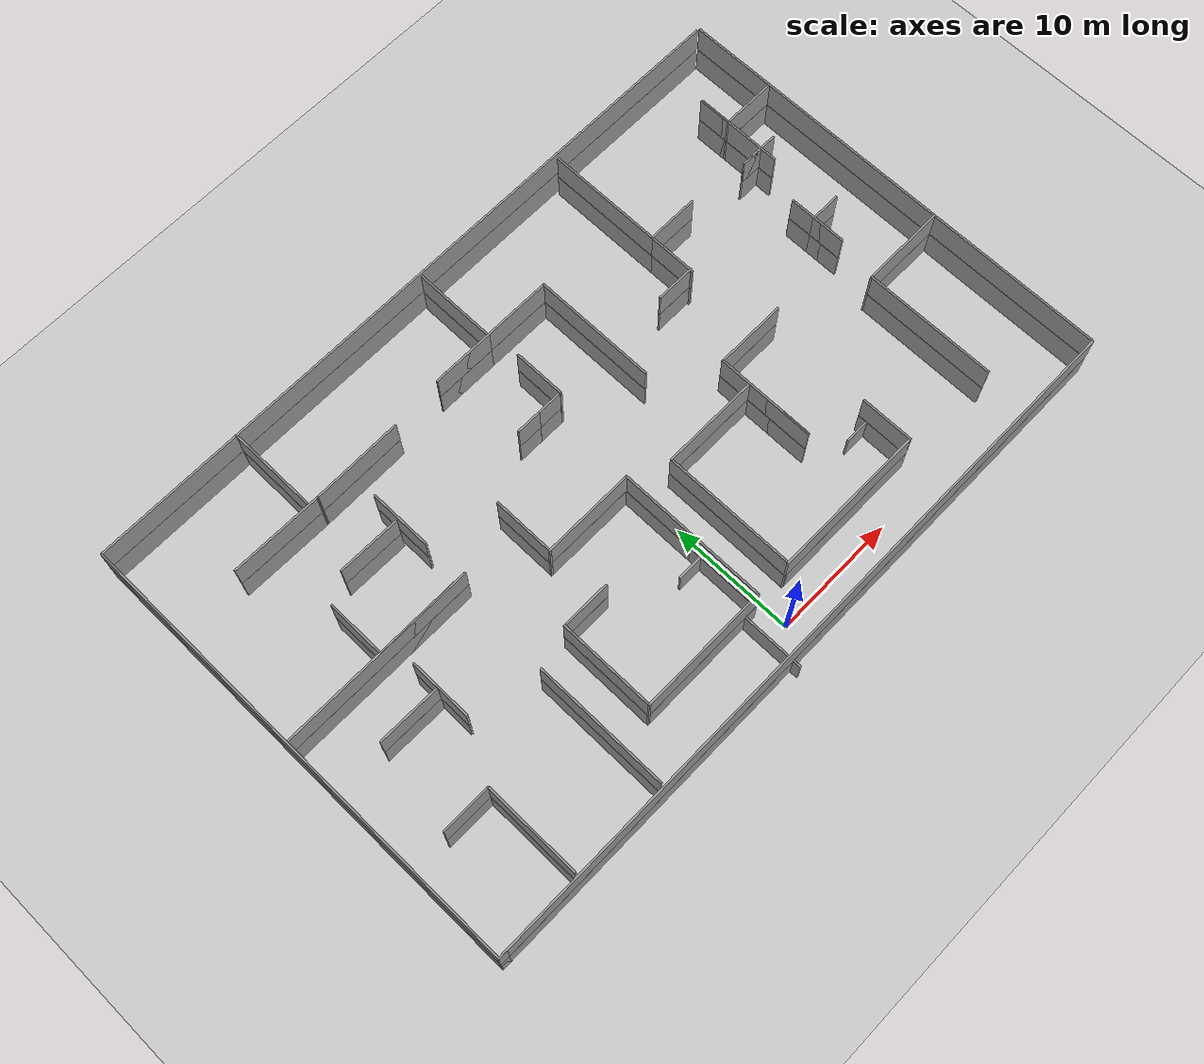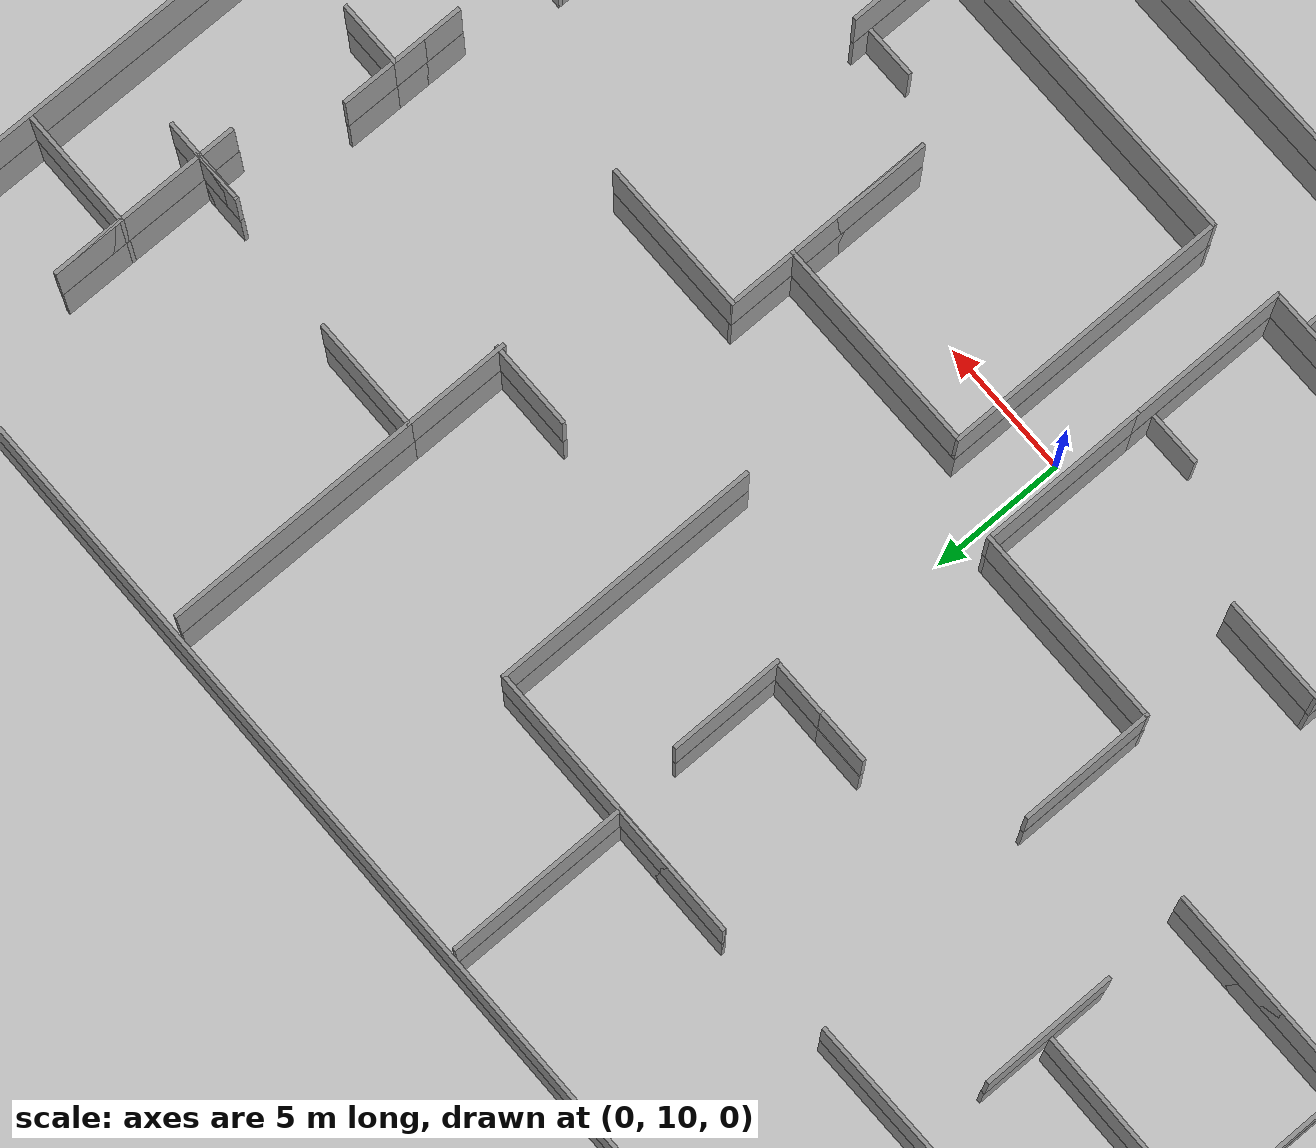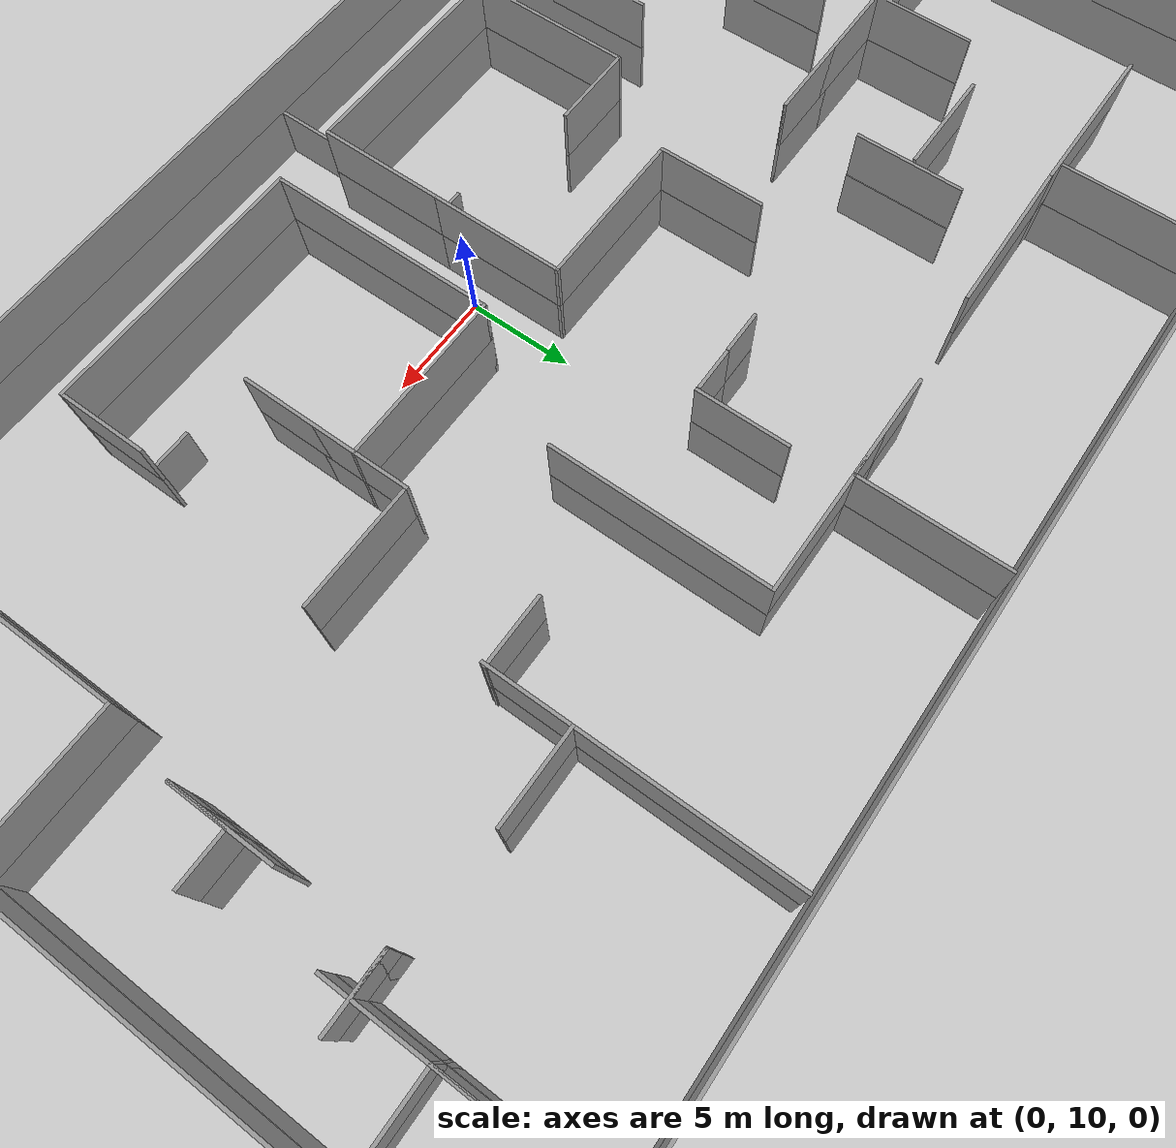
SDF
<sdf version="1.6">
 <world name="default">
  <light name="sun" type="directional">
   <pose>0 0 10 0 -0 0</pose>
   <diffuse>0.8 0.8 0.8 1</diffuse>
   <specular>0.2 0.2 0.2 1</specular>
   <attenuation>
    <range>1000</range>
    <constant>0.9</constant>
    <linear>0.01</linear>
    <quadratic>0.001</quadratic>
   </attenuation>
   <direction>-0.5 0.1 -0.9</direction>
  </light>
  <model name="ground_plane">
   <static>1</static>
   <link name="link">
    <collision name="collision">
     <geometry><plane><normal>0 0 1</normal><size>100 100</size></plane></geometry>
     <surface><friction><ode><mu>100</mu><mu2>50</mu2></ode></friction></surface>
    </collision>
    <visual name="visual">
     <cast_shadows>0</cast_shadows>
     <geometry><plane><normal>0 0 1</normal><size>100 100</size></plane></geometry>
     <material>
      <script><uri>file://media/materials/scripts/gazebo.material</uri><name>Gazebo/Grey</name></script>
     </material>
    </visual>
   </link>
  </model>
  <gravity>0 0 -9.8</gravity>
  <magnetic_field>6e-06 2.3e-05 -4.2e-05</magnetic_field>
  <atmosphere type="adiabatic"/>
  <physics name="default_physics" default="0" type="ode">
   <max_step_size>0.001</max_step_size>
   <real_time_factor>1</real_time_factor>
   <real_time_update_rate>1000</real_time_update_rate>
  </physics>
  <scene><ambient>0.4 0.4 0.4 1</ambient><background>0.7 0.7 0.7 1</background><shadows>1</shadows></scene>
  <audio><device>default</device></audio>
  <spherical_coordinates>
   <surface_model>EARTH_WGS84</surface_model>
   <latitude_deg>0</latitude_deg>
   <longitude_deg>0</longitude_deg>
   <elevation>0</elevation>
   <heading_deg>0</heading_deg>
  </spherical_coordinates>
  <model name="PaperTestRoom3">
   <pose>-0.1639 16.4774 0 0 -0 0</pose>
   <link name="Wall_12">
    <collision name="Wall_12_Collision">
     <geometry><box><size>7.36244 0.15 2.5</size></box></geometry>
     <pose>0 0 1.25 0 -0 0</pose>
    </collision>
    <visual name="Wall_12_Visual">
     <pose>0 0 1.25 0 -0 0</pose>
     <geometry><box><size>7.36244 0.15 2.5</size></box></geometry>
     <material>
      <script><uri>file://media/materials/scripts/gazebo.material</uri><name>Gazebo/Grey</name></script>
      <ambient>1 1 1 1</ambient>
     </material>
     <meta><layer>0</layer></meta>
    </visual>
    <pose>-19.953 11.4259 0 0 -0 -0.011282</pose>
   </link>
   <link name="Wall_16">
    <collision name="Wall_16_Collision">
     <geometry><box><size>7.75 0.15 2.5</size></box></geometry>
     <pose>0 0 1.25 0 -0 0</pose>
    </collision>
    <visual name="Wall_16_Visual">
     <pose>0 0 1.25 0 -0 0</pose>
     <geometry><box><size>7.75 0.15 2.5</size></box></geometry>
     <material>
      <script><uri>file://media/materials/scripts/gazebo.material</uri><name>Gazebo/Grey</name></script>
      <ambient>1 1 1 1</ambient>
     </material>
     <meta><layer>0</layer></meta>
    </visual>
    <pose>-22.0524 -14.5421 0 0 -0 1.5708</pose>
   </link>
   <link name="Wall_17">
    <collision name="Wall_17_Collision">
     <geometry><box><size>4 0.15 2.5</size></box></geometry>
     <pose>0 0 1.25 0 -0 0</pose>
    </collision>
    <visual name="Wall_17_Visual">
     <pose>0 0 1.25 0 -0 0</pose>
     <geometry><box><size>4 0.15 2.5</size></box></geometry>
     <material>
      <script><uri>file://media/materials/scripts/gazebo.material</uri><name>Gazebo/Grey</name></script>
      <ambient>1 1 1 1</ambient>
     </material>
     <meta><layer>0</layer></meta>
    </visual>
    <pose>-23.9774 -10.7421 0 0 -0 3.14159</pose>
   </link>
   <link name="Wall_19">
    <collision name="Wall_19_Collision">
     <geometry><box><size>10.75 0.15 2.5</size></box></geometry>
     <pose>0 0 1.25 0 -0 0</pose>
    </collision>
    <visual name="Wall_19_Visual">
     <pose>0 0 1.25 0 -0 0</pose>
     <geometry><box><size>10.75 0.15 2.5</size></box></geometry>
     <material>
      <script><uri>file://media/materials/scripts/gazebo.material</uri><name>Gazebo/Grey</name></script>
      <ambient>1 1 1 1</ambient>
     </material>
     <meta><layer>0</layer></meta>
    </visual>
    <pose>-14.3043 -13.0421 0 0 -0 1.5708</pose>
   </link>
   <link name="Wall_25">
    <collision name="Wall_25_Collision">
     <geometry><box><size>6 0.15 2.5</size></box></geometry>
     <pose>0 0 1.25 0 -0 0</pose>
    </collision>
    <visual name="Wall_25_Visual">
     <pose>0 0 1.25 0 -0 0</pose>
     <geometry><box><size>6 0.15 2.5</size></box></geometry>
     <material>
      <script><uri>file://media/materials/scripts/gazebo.material</uri><name>Gazebo/Grey</name></script>
      <ambient>1 1 1 1</ambient>
     </material>
     <meta><layer>0</layer></meta>
    </visual>
    <pose>-0.831101 -11.457 0 0 -0 1.5708</pose>
   </link>
   <link name="Wall_28">
    <collision name="Wall_28_Collision">
     <geometry><box><size>10.75 0.15 2.5</size></box></geometry>
     <pose>0 0 1.25 0 -0 0</pose>
    </collision>
    <visual name="Wall_28_Visual">
     <pose>0 0 1.25 0 -0 0</pose>
     <geometry><box><size>10.75 0.15 2.5</size></box></geometry>
     <material>
      <script><uri>file://media/materials/scripts/gazebo.material</uri><name>Gazebo/Grey</name></script>
      <ambient>1 1 1 1</ambient>
     </material>
     <meta><layer>0</layer></meta>
    </visual>
    <pose>2.16043 -9.0604 0 0 -0 1.5708</pose>
   </link>
   <link name="Wall_29">
    <collision name="Wall_29_Collision">
     <geometry><box><size>8 0.15 2.5</size></box></geometry>
     <pose>0 0 1.25 0 -0 0</pose>
    </collision>
    <visual name="Wall_29_Visual">
     <pose>0 0 1.25 0 -0 0</pose>
     <geometry><box><size>8 0.15 2.5</size></box></geometry>
     <material>
      <script><uri>file://media/materials/scripts/gazebo.material</uri><name>Gazebo/Grey</name></script>
      <ambient>1 1 1 1</ambient>
     </material>
     <meta><layer>0</layer></meta>
    </visual>
    <pose>6.08543 -3.7604 0 0 -0 0</pose>
   </link>
   <link name="Wall_30">
    <collision name="Wall_30_Collision">
     <geometry><box><size>5.5 0.15 2.5</size></box></geometry>
     <pose>0 0 1.25 0 -0 0</pose>
    </collision>
    <visual name="Wall_30_Visual">
     <pose>0 0 1.25 0 -0 0</pose>
     <geometry><box><size>5.5 0.15 2.5</size></box></geometry>
     <material>
      <script><uri>file://media/materials/scripts/gazebo.material</uri><name>Gazebo/Grey</name></script>
      <ambient>1 1 1 1</ambient>
     </material>
     <meta><layer>0</layer></meta>
    </visual>
    <pose>10.0104 -6.4354 0 0 -0 -1.5708</pose>
   </link>
   <link name="Wall_31">
    <collision name="Wall_31_Collision">
     <geometry><box><size>8 0.15 2.5</size></box></geometry>
     <pose>0 0 1.25 0 -0 0</pose>
    </collision>
    <visual name="Wall_31_Visual">
     <pose>0 0 1.25 0 -0 0</pose>
     <geometry><box><size>8 0.15 2.5</size></box></geometry>
     <material>
      <script><uri>file://media/materials/scripts/gazebo.material</uri><name>Gazebo/Grey</name></script>
      <ambient>1 1 1 1</ambient>
     </material>
     <meta><layer>0</layer></meta>
    </visual>
    <pose>10.0104 -5.1854 0 0 -0 1.5708</pose>
   </link>
   <link name="Wall_32">
    <collision name="Wall_32_Collision">
     <geometry><box><size>5.75 0.15 2.5</size></box></geometry>
     <pose>0 0 1.25 0 -0 0</pose>
    </collision>
    <visual name="Wall_32_Visual">
     <pose>0 0 1.25 0 -0 0</pose>
     <geometry><box><size>5.75 0.15 2.5</size></box></geometry>
     <material>
      <script><uri>file://media/materials/scripts/gazebo.material</uri><name>Gazebo/Grey</name></script>
      <ambient>1 1 1 1</ambient>
     </material>
     <meta><layer>0</layer></meta>
    </visual>
    <pose>12.8104 -1.2604 0 0 -0 0</pose>
   </link>
   <link name="Wall_34">
    <collision name="Wall_34_Collision">
     <geometry><box><size>12.5 0.15 2.5</size></box></geometry>
     <pose>0 0 1.25 0 -0 0</pose>
    </collision>
    <visual name="Wall_34_Visual">
     <pose>0 0 1.25 0 -0 0</pose>
     <geometry><box><size>12.5 0.15 2.5</size></box></geometry>
     <material>
      <script><uri>file://media/materials/scripts/gazebo.material</uri><name>Gazebo/Grey</name></script>
      <ambient>1 1 1 1</ambient>
     </material>
     <meta><layer>0</layer></meta>
    </visual>
    <pose>8.33543 -14.3604 0 0 -0 0</pose>
   </link>
   <link name="Wall_35">
    <collision name="Wall_35_Collision">
     <geometry><box><size>4.25 0.15 2.5</size></box></geometry>
     <pose>0 0 1.25 0 -0 0</pose>
    </collision>
    <visual name="Wall_35_Visual">
     <pose>0 0 1.25 0 -0 0</pose>
     <geometry><box><size>4.25 0.15 2.5</size></box></geometry>
     <material>
      <script><uri>file://media/materials/scripts/gazebo.material</uri><name>Gazebo/Grey</name></script>
      <ambient>1 1 1 1</ambient>
     </material>
     <meta><layer>0</layer></meta>
    </visual>
    <pose>14.5104 -12.3104 0 0 -0 1.5708</pose>
   </link>
   <link name="Wall_37">
    <collision name="Wall_37_Collision">
     <geometry><box><size>10.5 0.15 2.5</size></box></geometry>
     <pose>0 0 1.25 0 -0 0</pose>
    </collision>
    <visual name="Wall_37_Visual">
     <pose>0 0 1.25 0 -0 0</pose>
     <geometry><box><size>10.5 0.15 2.5</size></box></geometry>
     <material>
      <script><uri>file://media/materials/scripts/gazebo.material</uri><name>Gazebo/Grey</name></script>
      <ambient>1 1 1 1</ambient>
     </material>
     <meta><layer>0</layer></meta>
    </visual>
    <pose>-6.0061 -14.382 0 0 -0 3.14159</pose>
   </link>
   <link name="Wall_38">
    <collision name="Wall_38_Collision">
     <geometry><box><size>7.75 0.15 2.5</size></box></geometry>
     <pose>0 0 1.25 0 -0 0</pose>
    </collision>
    <visual name="Wall_38_Visual">
     <pose>0 0 1.25 0 -0 0</pose>
     <geometry><box><size>7.75 0.15 2.5</size></box></geometry>
     <material>
      <script><uri>file://media/materials/scripts/gazebo.material</uri><name>Gazebo/Grey</name></script>
      <ambient>1 1 1 1</ambient>
     </material>
     <meta><layer>0</layer></meta>
    </visual>
    <pose>-11.1811 -10.582 0 0 -0 1.5708</pose>
   </link>
   <link name="Wall_39">
    <collision name="Wall_39_Collision">
     <geometry><box><size>4 0.15 2.5</size></box></geometry>
     <pose>0 0 1.25 0 -0 0</pose>
    </collision>
    <visual name="Wall_39_Visual">
     <pose>0 0 1.25 0 -0 0</pose>
     <geometry><box><size>4 0.15 2.5</size></box></geometry>
     <material>
      <script><uri>file://media/materials/scripts/gazebo.material</uri><name>Gazebo/Grey</name></script>
      <ambient>1 1 1 1</ambient>
     </material>
     <meta><layer>0</layer></meta>
    </visual>
    <pose>-9.2561 -6.78202 0 0 -0 0</pose>
   </link>
   <link name="Wall_42">
    <collision name="Wall_42_Collision">
     <geometry><box><size>6.25 0.15 2.5</size></box></geometry>
     <pose>0 0 1.25 0 -0 0</pose>
    </collision>
    <visual name="Wall_42_Visual">
     <pose>0 0 1.25 0 -0 0</pose>
     <geometry><box><size>6.25 0.15 2.5</size></box></geometry>
     <material>
      <script><uri>file://media/materials/scripts/gazebo.material</uri><name>Gazebo/Grey</name></script>
      <ambient>1 1 1 1</ambient>
     </material>
     <meta><layer>0</layer></meta>
    </visual>
    <pose>-0.831101 -5.48202 0 0 -0 1.5708</pose>
   </link>
   <link name="Wall_43">
    <collision name="Wall_43_Collision">
     <geometry><box><size>7.5 0.15 2.5</size></box></geometry>
     <pose>0 0 1.25 0 -0 0</pose>
    </collision>
    <visual name="Wall_43_Visual">
     <pose>0 0 1.25 0 -0 0</pose>
     <geometry><box><size>7.5 0.15 2.5</size></box></geometry>
     <material>
      <script><uri>file://media/materials/scripts/gazebo.material</uri><name>Gazebo/Grey</name></script>
      <ambient>1 1 1 1</ambient>
     </material>
     <meta><layer>0</layer></meta>
    </visual>
    <pose>-4.5061 -2.43202 0 0 -0 3.14159</pose>
   </link>
   <link name="Wall_44">
    <collision name="Wall_44_Collision">
     <geometry><box><size>5 0.15 2.5</size></box></geometry>
     <pose>0 0 1.25 0 -0 0</pose>
    </collision>
    <visual name="Wall_44_Visual">
     <pose>0 0 1.25 0 -0 0</pose>
     <geometry><box><size>5 0.15 2.5</size></box></geometry>
     <material>
      <script><uri>file://media/materials/scripts/gazebo.material</uri><name>Gazebo/Grey</name></script>
      <ambient>1 1 1 1</ambient>
     </material>
     <meta><layer>0</layer></meta>
    </visual>
    <pose>-8.1811 -0.007024 0 0 -0 1.5708</pose>
   </link>
   <link name="Wall_47">
    <collision name="Wall_47_Collision">
     <geometry><box><size>37.25 0.15 2.5</size></box></geometry>
     <pose>0 0 1.25 0 -0 0</pose>
    </collision>
    <visual name="Wall_47_Visual">
     <pose>0 0 1.25 0 -0 0</pose>
     <geometry><box><size>37.25 0.15 2.5</size></box></geometry>
     <material>
      <script><uri>file://media/materials/scripts/gazebo.material</uri><name>Gazebo/Grey</name></script>
      <ambient>1 1 1 1</ambient>
     </material>
     <meta><layer>0</layer></meta>
    </visual>
    <pose>28.9541 -0.022609 0 0 -0 1.5708</pose>
   </link>
   <link name="Wall_49">
    <collision name="Wall_49_Collision">
     <geometry><box><size>7 0.15 2.5</size></box></geometry>
     <pose>0 0 1.25 0 -0 0</pose>
    </collision>
    <visual name="Wall_49_Visual">
     <pose>0 0 1.25 0 -0 0</pose>
     <geometry><box><size>7 0.15 2.5</size></box></geometry>
     <material>
      <script><uri>file://media/materials/scripts/gazebo.material</uri><name>Gazebo/Grey</name></script>
      <ambient>1 1 1 1</ambient>
     </material>
     <meta><layer>0</layer></meta>
    </visual>
    <pose>25.5161 -4.34601 0 0 -0 3.14159</pose>
   </link>
   <link name="Wall_5">
    <collision name="Wall_5_Collision">
     <geometry><box><size>0.75 0.15 2.5</size></box></geometry>
     <pose>0 0 1.25 0 -0 0</pose>
    </collision>
    <visual name="Wall_5_Visual">
     <pose>0 0 1.25 0 -0 0</pose>
     <geometry><box><size>0.75 0.15 2.5</size></box></geometry>
     <material>
      <script><uri>file://media/materials/scripts/gazebo.material</uri><name>Gazebo/Grey</name></script>
      <ambient>1 1 1 1</ambient>
     </material>
     <meta><layer>0</layer></meta>
    </visual>
    <pose>-28.6541 -18.6782 0 0 -0 3.14159</pose>
   </link>
   <link name="Wall_50">
    <collision name="Wall_50_Collision">
     <geometry><box><size>10.75 0.15 2.5</size></box></geometry>
     <pose>0 0 1.25 0 -0 0</pose>
    </collision>
    <visual name="Wall_50_Visual">
     <pose>0 0 1.25 0 -0 0</pose>
     <geometry><box><size>10.75 0.15 2.5</size></box></geometry>
     <material>
      <script><uri>file://media/materials/scripts/gazebo.material</uri><name>Gazebo/Grey</name></script>
      <ambient>1 1 1 1</ambient>
     </material>
     <meta><layer>0</layer></meta>
    </visual>
    <pose>22.0911 -9.64601 0 0 -0 -1.5708</pose>
   </link>
   <link name="Wall_52">
    <collision name="Wall_52_Collision">
     <geometry><box><size>4.5 0.15 2.5</size></box></geometry>
     <pose>0 0 1.25 0 -0 0</pose>
    </collision>
    <visual name="Wall_52_Visual">
     <pose>0 0 1.25 0 -0 0</pose>
     <geometry><box><size>4.5 0.15 2.5</size></box></geometry>
     <material>
      <script><uri>file://media/materials/scripts/gazebo.material</uri><name>Gazebo/Grey</name></script>
      <ambient>1 1 1 1</ambient>
     </material>
     <meta><layer>0</layer></meta>
    </visual>
    <pose>26.6525 11.5563 0 0 -0 3.14159</pose>
   </link>
   <link name="Wall_53">
    <collision name="Wall_53_Collision">
     <geometry><box><size>2.75 0.15 2.5</size></box></geometry>
     <pose>0 0 1.25 0 -0 0</pose>
    </collision>
    <visual name="Wall_53_Visual">
     <pose>0 0 1.25 0 -0 0</pose>
     <geometry><box><size>2.75 0.15 2.5</size></box></geometry>
     <material>
      <script><uri>file://media/materials/scripts/gazebo.material</uri><name>Gazebo/Grey</name></script>
      <ambient>1 1 1 1</ambient>
     </material>
     <meta><layer>0</layer></meta>
    </visual>
    <pose>24.4775 12.8563 0 0 -0 1.5708</pose>
   </link>
   <link name="Wall_54">
    <collision name="Wall_54_Collision">
     <geometry><box><size>7.25 0.15 2.5</size></box></geometry>
     <pose>0 0 1.25 0 -0 0</pose>
    </collision>
    <visual name="Wall_54_Visual">
     <pose>0 0 1.25 0 -0 0</pose>
     <geometry><box><size>7.25 0.15 2.5</size></box></geometry>
     <material>
      <script><uri>file://media/materials/scripts/gazebo.material</uri><name>Gazebo/Grey</name></script>
      <ambient>1 1 1 1</ambient>
     </material>
     <meta><layer>0</layer></meta>
    </visual>
    <pose>24.4775 10.6063 0 0 -0 -1.5708</pose>
   </link>
   <link name="Wall_57">
    <collision name="Wall_57_Collision">
     <geometry><box><size>2 0.15 2.5</size></box></geometry>
     <pose>0 0 1.25 0 -0 0</pose>
    </collision>
    <visual name="Wall_57_Visual">
     <pose>0 0 1.25 0 -0 0</pose>
     <geometry><box><size>2 0.15 2.5</size></box></geometry>
     <material>
      <script><uri>file://media/materials/scripts/gazebo.material</uri><name>Gazebo/Grey</name></script>
      <ambient>1 1 1 1</ambient>
     </material>
     <meta><layer>0</layer></meta>
    </visual>
    <pose>23.6283 8.34759 0 0 -0 3.14159</pose>
   </link>
   <link name="Wall_58">
    <collision name="Wall_58_Collision">
     <geometry><box><size>3.25 0.15 2.5</size></box></geometry>
     <pose>0 0 1.25 0 -0 0</pose>
    </collision>
    <visual name="Wall_58_Visual">
     <pose>0 0 1.25 0 -0 0</pose>
     <geometry><box><size>3.25 0.15 2.5</size></box></geometry>
     <material>
      <script><uri>file://media/materials/scripts/gazebo.material</uri><name>Gazebo/Grey</name></script>
      <ambient>1 1 1 1</ambient>
     </material>
     <meta><layer>0</layer></meta>
    </visual>
    <pose>24.2533 8.34759 0 0 -0 0</pose>
   </link>
   <link name="Wall_6">
    <collision name="Wall_6_Collision">
     <geometry><box><size>37.5 0.15 2.5</size></box></geometry>
     <pose>0 0 1.25 0 -0 0</pose>
    </collision>
    <visual name="Wall_6_Visual">
     <pose>0 0 1.25 0 -0 0</pose>
     <geometry><box><size>37.5 0.15 2.5</size></box></geometry>
     <material>
      <script><uri>file://media/materials/scripts/gazebo.material</uri><name>Gazebo/Grey</name></script>
      <ambient>1 1 1 1</ambient>
     </material>
     <meta><layer>0</layer></meta>
    </visual>
    <pose>-28.9541 -0.003198 0 0 -0 1.5708</pose>
   </link>
   <link name="Wall_60">
    <collision name="Wall_60_Collision">
     <geometry><box><size>9.5 0.15 2.5</size></box></geometry>
     <pose>0 0 1.25 0 -0 0</pose>
    </collision>
    <visual name="Wall_60_Visual">
     <pose>0 0 1.25 0 -0 0</pose>
     <geometry><box><size>9.5 0.15 2.5</size></box></geometry>
     <material>
      <script><uri>file://media/materials/scripts/gazebo.material</uri><name>Gazebo/Grey</name></script>
      <ambient>1 1 1 1</ambient>
     </material>
     <meta><layer>0</layer></meta>
    </visual>
    <pose>13.6263 13.5981 0 0 -0 -1.5708</pose>
   </link>
   <link name="Wall_61">
    <collision name="Wall_61_Collision">
     <geometry><box><size>4.25 0.15 2.5</size></box></geometry>
     <pose>0 0 1.25 0 -0 0</pose>
    </collision>
    <visual name="Wall_61_Visual">
     <pose>0 0 1.25 0 -0 0</pose>
     <geometry><box><size>4.25 0.15 2.5</size></box></geometry>
     <material>
      <script><uri>file://media/materials/scripts/gazebo.material</uri><name>Gazebo/Grey</name></script>
      <ambient>1 1 1 1</ambient>
     </material>
     <meta><layer>0</layer></meta>
    </visual>
    <pose>15.6763 8.92306 0 0 -0 0</pose>
   </link>
   <link name="Wall_64">
    <collision name="Wall_64_Collision">
     <geometry><box><size>6.75 0.15 2.5</size></box></geometry>
     <pose>0 0 1.25 0 -0 0</pose>
    </collision>
    <visual name="Wall_64_Visual">
     <pose>0 0 1.25 0 -0 0</pose>
     <geometry><box><size>6.75 0.15 2.5</size></box></geometry>
     <material>
      <script><uri>file://media/materials/scripts/gazebo.material</uri><name>Gazebo/Grey</name></script>
      <ambient>1 1 1 1</ambient>
     </material>
     <meta><layer>0</layer></meta>
    </visual>
    <pose>0.10616 15.1154 0 0 -0 -1.5708</pose>
   </link>
   <link name="Wall_65">
    <collision name="Wall_65_Collision">
     <geometry><box><size>5 0.15 2.5</size></box></geometry>
     <pose>0 0 1.25 0 -0 0</pose>
    </collision>
    <visual name="Wall_65_Visual">
     <pose>0 0 1.25 0 -0 0</pose>
     <geometry><box><size>5 0.15 2.5</size></box></geometry>
     <material>
      <script><uri>file://media/materials/scripts/gazebo.material</uri><name>Gazebo/Grey</name></script>
      <ambient>1 1 1 1</ambient>
     </material>
     <meta><layer>0</layer></meta>
    </visual>
    <pose>-2.31884 11.8154 0 0 -0 3.14159</pose>
   </link>
   <link name="Wall_66">
    <collision name="Wall_66_Collision">
     <geometry><box><size>10.5 0.15 2.5</size></box></geometry>
     <pose>0 0 1.25 0 -0 0</pose>
    </collision>
    <visual name="Wall_66_Visual">
     <pose>0 0 1.25 0 -0 0</pose>
     <geometry><box><size>10.5 0.15 2.5</size></box></geometry>
     <material>
      <script><uri>file://media/materials/scripts/gazebo.material</uri><name>Gazebo/Grey</name></script>
      <ambient>1 1 1 1</ambient>
     </material>
     <meta><layer>0</layer></meta>
    </visual>
    <pose>0.431161 11.8154 0 0 -0 0</pose>
   </link>
   <link name="Wall_67">
    <collision name="Wall_67_Collision">
     <geometry><box><size>10 0.15 2.5</size></box></geometry>
     <pose>0 0 1.25 0 -0 0</pose>
    </collision>
    <visual name="Wall_67_Visual">
     <pose>0 0 1.25 0 -0 0</pose>
     <geometry><box><size>10 0.15 2.5</size></box></geometry>
     <material>
      <script><uri>file://media/materials/scripts/gazebo.material</uri><name>Gazebo/Grey</name></script>
      <ambient>1 1 1 1</ambient>
     </material>
     <meta><layer>0</layer></meta>
    </visual>
    <pose>5.60616 6.89038 0 0 -0 -1.5708</pose>
   </link>
   <link name="Wall_69">
    <collision name="Wall_69_Collision">
     <geometry><box><size>15.75 0.15 2.5</size></box></geometry>
     <pose>0 0 1.25 0 -0 0</pose>
    </collision>
    <visual name="Wall_69_Visual">
     <pose>0 0 1.25 0 -0 0</pose>
     <geometry><box><size>15.75 0.15 2.5</size></box></geometry>
     <material>
      <script><uri>file://media/materials/scripts/gazebo.material</uri><name>Gazebo/Grey</name></script>
      <ambient>1 1 1 1</ambient>
     </material>
     <meta><layer>0</layer></meta>
    </visual>
    <pose>-20.9843 0.483346 0 0 -0 0</pose>
   </link>
   <link name="Wall_70">
    <collision name="Wall_70_Collision">
     <geometry><box><size>7.75 0.15 2.5</size></box></geometry>
     <pose>0 0 1.25 0 -0 0</pose>
    </collision>
    <visual name="Wall_70_Visual">
     <pose>0 0 1.25 0 -0 0</pose>
     <geometry><box><size>7.75 0.15 2.5</size></box></geometry>
     <material>
      <script><uri>file://media/materials/scripts/gazebo.material</uri><name>Gazebo/Grey</name></script>
      <ambient>1 1 1 1</ambient>
     </material>
     <meta><layer>0</layer></meta>
    </visual>
    <pose>-16.9843 0.483346 0 0 -0 3.14159</pose>
   </link>
   <link name="Wall_71">
    <collision name="Wall_71_Collision">
     <geometry><box><size>4.75 0.15 2.5</size></box></geometry>
     <pose>0 0 1.25 0 -0 0</pose>
    </collision>
    <visual name="Wall_71_Visual">
     <pose>0 0 1.25 0 -0 0</pose>
     <geometry><box><size>4.75 0.15 2.5</size></box></geometry>
     <material>
      <script><uri>file://media/materials/scripts/gazebo.material</uri><name>Gazebo/Grey</name></script>
      <ambient>1 1 1 1</ambient>
     </material>
     <meta><layer>0</layer></meta>
    </visual>
    <pose>-20.7843 2.78335 0 0 -0 1.5708</pose>
   </link>
   <link name="Wall_73">
    <collision name="Wall_73_Collision">
     <geometry><box><size>58 0.15 2.5</size></box></geometry>
     <pose>0 0 1.25 0 -0 0</pose>
    </collision>
    <visual name="Wall_73_Visual">
     <pose>0 0 1.25 0 -0 0</pose>
     <geometry><box><size>58 0.15 2.5</size></box></geometry>
     <material>
      <script><uri>file://media/materials/scripts/gazebo.material</uri><name>Gazebo/Grey</name></script>
      <ambient>1 1 1 1</ambient>
     </material>
     <meta><layer>0</layer></meta>
    </visual>
    <pose>-0.029105 -18.6782 0 0 -0 0</pose>
   </link>
   <link name="Wall_75">
    <collision name="Wall_75_Collision">
     <geometry><box><size>57.75 0.15 2.5</size></box></geometry>
     <pose>0 0 1.25 0 -0 0</pose>
    </collision>
    <visual name="Wall_75_Visual">
     <pose>0 0 1.25 0 -0 0</pose>
     <geometry><box><size>57.75 0.15 2.5</size></box></geometry>
     <material>
      <script><uri>file://media/materials/scripts/gazebo.material</uri><name>Gazebo/Grey</name></script>
      <ambient>1 1 1 1</ambient>
     </material>
     <meta><layer>0</layer></meta>
    </visual>
    <pose>-0.154105 18.6718 0 0 -0 0</pose>
   </link>
   <link name="Wall_77">
    <collision name="Wall_77_Collision">
     <geometry><box><size>7.38848 0.15 2.5</size></box></geometry>
     <pose>0 0 1.25 0 -0 0</pose>
    </collision>
    <visual name="Wall_77_Visual">
     <pose>0 0 1.25 0 -0 0</pose>
     <geometry><box><size>7.38848 0.15 2.5</size></box></geometry>
     <material>
      <script><uri>file://media/materials/scripts/gazebo.material</uri><name>Gazebo/Grey</name></script>
      <ambient>1 1 1 1</ambient>
     </material>
     <meta><layer>0</layer></meta>
    </visual>
    <pose>-12.728 11.4259 0 0 -0 0.011242</pose>
   </link>
   <link name="Wall_79">
    <collision name="Wall_79_Collision">
     <geometry><box><size>7.25 0.15 2.5</size></box></geometry>
     <pose>0 0 1.25 0 -0 0</pose>
    </collision>
    <visual name="Wall_79_Visual">
     <pose>0 0 1.25 0 -0 0</pose>
     <geometry><box><size>7.25 0.15 2.5</size></box></geometry>
     <material>
      <script><uri>file://media/materials/scripts/gazebo.material</uri><name>Gazebo/Grey</name></script>
      <ambient>1 1 1 1</ambient>
     </material>
     <meta><layer>0</layer></meta>
    </visual>
    <pose>-17.0746 15.1282 0 0 -0 1.5708</pose>
   </link>
   <link name="Wall_83">
    <collision name="Wall_83_Collision">
     <geometry><box><size>4.25 0.15 2.5</size></box></geometry>
     <pose>0 0 1.25 0 -0 0</pose>
    </collision>
    <visual name="Wall_83_Visual">
     <pose>0 0 1.25 0 -0 0</pose>
     <geometry><box><size>4.25 0.15 2.5</size></box></geometry>
     <material>
      <script><uri>file://media/materials/scripts/gazebo.material</uri><name>Gazebo/Grey</name></script>
      <ambient>1 1 1 1</ambient>
     </material>
     <meta><layer>0</layer></meta>
    </visual>
    <pose>0.487926 7.17144 0 0 -0 1.5708</pose>
   </link>
   <link name="Wall_85">
    <collision name="Wall_85_Collision">
     <geometry><box><size>4.75 0.15 2.5</size></box></geometry>
     <pose>0 0 1.25 0 -0 0</pose>
    </collision>
    <visual name="Wall_85_Visual">
     <pose>0 0 1.25 0 -0 0</pose>
     <geometry><box><size>4.75 0.15 2.5</size></box></geometry>
     <material>
      <script><uri>file://media/materials/scripts/gazebo.material</uri><name>Gazebo/Grey</name></script>
      <ambient>1 1 1 1</ambient>
     </material>
     <meta><layer>0</layer></meta>
    </visual>
    <pose>22.8497 1.42247 0 0 -0 -1.5708</pose>
   </link>
   <link name="Wall_86">
    <collision name="Wall_86_Collision">
     <geometry><box><size>2.75 0.15 2.5</size></box></geometry>
     <pose>0 0 1.25 0 -0 0</pose>
    </collision>
    <visual name="Wall_86_Visual">
     <pose>0 0 1.25 0 -0 0</pose>
     <geometry><box><size>2.75 0.15 2.5</size></box></geometry>
     <material>
      <script><uri>file://media/materials/scripts/gazebo.material</uri><name>Gazebo/Grey</name></script>
      <ambient>1 1 1 1</ambient>
     </material>
     <meta><layer>0</layer></meta>
    </visual>
    <pose>22.8497 0.422475 0 0 -0 1.5708</pose>
   </link>
   <link name="Wall_87">
    <collision name="Wall_87_Collision">
     <geometry><box><size>2.5 0.15 2.5</size></box></geometry>
     <pose>0 0 1.25 0 -0 0</pose>
    </collision>
    <visual name="Wall_87_Visual">
     <pose>0 0 1.25 0 -0 0</pose>
     <geometry><box><size>2.5 0.15 2.5</size></box></geometry>
     <material>
      <script><uri>file://media/materials/scripts/gazebo.material</uri><name>Gazebo/Grey</name></script>
      <ambient>1 1 1 1</ambient>
     </material>
     <meta><layer>0</layer></meta>
    </visual>
    <pose>24.0247 1.72248 0 0 -0 0</pose>
   </link>
   <link name="Wall_89">
    <collision name="Wall_89_Collision">
     <geometry><box><size>4 0.15 2.5</size></box></geometry>
     <pose>0 0 1.25 0 -0 0</pose>
    </collision>
    <visual name="Wall_89_Visual">
     <pose>0 0 1.25 0 -0 0</pose>
     <geometry><box><size>4 0.15 2.5</size></box></geometry>
     <material>
      <script><uri>file://media/materials/scripts/gazebo.material</uri><name>Gazebo/Grey</name></script>
      <ambient>1 1 1 1</ambient>
     </material>
     <meta><layer>0</layer></meta>
    </visual>
    <pose>13.6263 6.99806 0 0 -0 -1.5708</pose>
   </link>
   <link name="Wall_91">
    <collision name="Wall_91_Collision">
     <geometry><box><size>3.25 0.15 2.5</size></box></geometry>
     <pose>0 0 1.25 0 -0 0</pose>
    </collision>
    <visual name="Wall_91_Visual">
     <pose>0 0 1.25 0 -0 0</pose>
     <geometry><box><size>3.25 0.15 2.5</size></box></geometry>
     <material>
      <script><uri>file://media/materials/scripts/gazebo.material</uri><name>Gazebo/Grey</name></script>
      <ambient>1 1 1 1</ambient>
     </material>
     <meta><layer>0</layer></meta>
    </visual>
    <pose>12.1319 5.22905 0 0 -0 0</pose>
   </link>
   <static>1</static>
  </model>
  <model name="5mWall">
   <pose>-16.4333 22.9104 2.46833 0 -0 1.56041</pose>
   <link name="Wall_0">
    <collision name="Wall_0_Collision">
     <geometry><box><size>5 0.15 2.5</size></box></geometry>
     <pose>0 0 1.25 0 -0 0</pose>
    </collision>
    <visual name="Wall_0_Visual">
     <pose>0 0 1.25 0 -0 0</pose>
     <geometry><box><size>5 0.15 2.5</size></box></geometry>
     <material>
      <script><uri>file://media/materials/scripts/gazebo.material</uri><name>Gazebo/Grey</name></script>
      <ambient>1 1 1 1</ambient>
     </material>
     <meta><layer>0</layer></meta>
    </visual>
    <pose>0 -0 0 0 -0 1.5708</pose>
   </link>
   <static>1</static>
  </model>
  <model name="5mWall_0">
   <pose>-13.7019 22.7697 2.48433 0 -0 0</pose>
   <link name="Wall_0">
    <collision name="Wall_0_Collision">
     <geometry><box><size>5 0.15 2.5</size></box></geometry>
     <pose>0 0 1.25 0 -0 0</pose>
    </collision>
    <visual name="Wall_0_Visual">
     <pose>0 0 1.25 0 -0 0</pose>
     <geometry><box><size>5 0.15 2.5</size></box></geometry>
     <material>
      <script><uri>file://media/materials/scripts/gazebo.material</uri><name>Gazebo/Grey</name></script>
      <ambient>1 1 1 1</ambient>
     </material>
     <meta><layer>0</layer></meta>
    </visual>
    <pose>0 -0 0 0 -0 1.5708</pose>
   </link>
   <static>1</static>
  </model>
  <model name="5mWall_0_clone">
   <pose>-19.9182 12.476 2.47371 0 -0 0</pose>
   <link name="Wall_0">
    <collision name="Wall_0_Collision">
     <geometry><box><size>5 0.15 2.5</size></box></geometry>
     <pose>0 0 1.25 0 -0 0</pose>
    </collision>
    <visual name="Wall_0_Visual">
     <pose>0 0 1.25 0 -0 0</pose>
     <geometry><box><size>5 0.15 2.5</size></box></geometry>
     <material>
      <script><uri>file://media/materials/scripts/gazebo.material</uri><name>Gazebo/Grey</name></script>
      <ambient>1 1 1 1</ambient>
     </material>
     <meta><layer>0</layer></meta>
    </visual>
    <pose>0 -0 0 0 -0 1.5708</pose>
   </link>
   <static>1</static>
  </model>
  <model name="5mWall_clone">
   <pose>-22.4986 12.6897 2.46346 0 -0 1.56041</pose>
   <link name="Wall_0">
    <collision name="Wall_0_Collision">
     <geometry><box><size>5 0.15 2.5</size></box></geometry>
     <pose>0 0 1.25 0 -0 0</pose>
    </collision>
    <visual name="Wall_0_Visual">
     <pose>0 0 1.25 0 -0 0</pose>
     <geometry><box><size>5 0.15 2.5</size></box></geometry>
     <material>
      <script><uri>file://media/materials/scripts/gazebo.material</uri><name>Gazebo/Grey</name></script>
      <ambient>1 1 1 1</ambient>
     </material>
     <meta><layer>0</layer></meta>
    </visual>
    <pose>0 -0 0 0 -0 1.5708</pose>
   </link>
   <static>1</static>
  </model>
  <model name="PaperTestRoom3_0">
   <pose>-0.1541 16.4874 2.5 0 -0 0</pose>
   <link name="Wall_12">
    <collision name="Wall_12_Collision">
     <geometry><box><size>7.36244 0.15 2.5</size></box></geometry>
     <pose>0 0 1.25 0 -0 0</pose>
    </collision>
    <visual name="Wall_12_Visual">
     <pose>0 0 1.25 0 -0 0</pose>
     <geometry><box><size>7.36244 0.15 2.5</size></box></geometry>
     <material>
      <script><uri>file://media/materials/scripts/gazebo.material</uri><name>Gazebo/Grey</name></script>
      <ambient>1 1 1 1</ambient>
     </material>
     <meta><layer>0</layer></meta>
    </visual>
    <pose>-19.953 11.4259 0 0 -0 -0.011282</pose>
   </link>
   <link name="Wall_16">
    <collision name="Wall_16_Collision">
     <geometry><box><size>7.75 0.15 2.5</size></box></geometry>
     <pose>0 0 1.25 0 -0 0</pose>
    </collision>
    <visual name="Wall_16_Visual">
     <pose>0 0 1.25 0 -0 0</pose>
     <geometry><box><size>7.75 0.15 2.5</size></box></geometry>
     <material>
      <script><uri>file://media/materials/scripts/gazebo.material</uri><name>Gazebo/Grey</name></script>
      <ambient>1 1 1 1</ambient>
     </material>
     <meta><layer>0</layer></meta>
    </visual>
    <pose>-22.0524 -14.5421 0 0 -0 1.5708</pose>
   </link>
   <link name="Wall_17">
    <collision name="Wall_17_Collision">
     <geometry><box><size>4 0.15 2.5</size></box></geometry>
     <pose>0 0 1.25 0 -0 0</pose>
    </collision>
    <visual name="Wall_17_Visual">
     <pose>0 0 1.25 0 -0 0</pose>
     <geometry><box><size>4 0.15 2.5</size></box></geometry>
     <material>
      <script><uri>file://media/materials/scripts/gazebo.material</uri><name>Gazebo/Grey</name></script>
      <ambient>1 1 1 1</ambient>
     </material>
     <meta><layer>0</layer></meta>
    </visual>
    <pose>-23.9774 -10.7421 0 0 -0 3.14159</pose>
   </link>
   <link name="Wall_19">
    <collision name="Wall_19_Collision">
     <geometry><box><size>10.75 0.15 2.5</size></box></geometry>
     <pose>0 0 1.25 0 -0 0</pose>
    </collision>
    <visual name="Wall_19_Visual">
     <pose>0 0 1.25 0 -0 0</pose>
     <geometry><box><size>10.75 0.15 2.5</size></box></geometry>
     <material>
      <script><uri>file://media/materials/scripts/gazebo.material</uri><name>Gazebo/Grey</name></script>
      <ambient>1 1 1 1</ambient>
     </material>
     <meta><layer>0</layer></meta>
    </visual>
    <pose>-14.3043 -13.0421 0 0 -0 1.5708</pose>
   </link>
   <link name="Wall_25">
    <collision name="Wall_25_Collision">
     <geometry><box><size>6 0.15 2.5</size></box></geometry>
     <pose>0 0 1.25 0 -0 0</pose>
    </collision>
    <visual name="Wall_25_Visual">
     <pose>0 0 1.25 0 -0 0</pose>
     <geometry><box><size>6 0.15 2.5</size></box></geometry>
     <material>
      <script><uri>file://media/materials/scripts/gazebo.material</uri><name>Gazebo/Grey</name></script>
      <ambient>1 1 1 1</ambient>
     </material>
     <meta><layer>0</layer></meta>
    </visual>
    <pose>-0.831101 -11.457 0 0 -0 1.5708</pose>
   </link>
   <link name="Wall_28">
    <collision name="Wall_28_Collision">
     <geometry><box><size>10.75 0.15 2.5</size></box></geometry>
     <pose>0 0 1.25 0 -0 0</pose>
    </collision>
    <visual name="Wall_28_Visual">
     <pose>0 0 1.25 0 -0 0</pose>
     <geometry><box><size>10.75 0.15 2.5</size></box></geometry>
     <material>
      <script><uri>file://media/materials/scripts/gazebo.material</uri><name>Gazebo/Grey</name></script>
      <ambient>1 1 1 1</ambient>
     </material>
     <meta><layer>0</layer></meta>
    </visual>
    <pose>2.16043 -9.0604 0 0 -0 1.5708</pose>
   </link>
   <link name="Wall_29">
    <collision name="Wall_29_Collision">
     <geometry><box><size>8 0.15 2.5</size></box></geometry>
     <pose>0 0 1.25 0 -0 0</pose>
    </collision>
    <visual name="Wall_29_Visual">
     <pose>0 0 1.25 0 -0 0</pose>
     <geometry><box><size>8 0.15 2.5</size></box></geometry>
     <material>
      <script><uri>file://media/materials/scripts/gazebo.material</uri><name>Gazebo/Grey</name></script>
      <ambient>1 1 1 1</ambient>
     </material>
     <meta><layer>0</layer></meta>
    </visual>
    <pose>6.08543 -3.7604 0 0 -0 0</pose>
   </link>
   <link name="Wall_30">
    <collision name="Wall_30_Collision">
     <geometry><box><size>5.5 0.15 2.5</size></box></geometry>
     <pose>0 0 1.25 0 -0 0</pose>
    </collision>
    <visual name="Wall_30_Visual">
     <pose>0 0 1.25 0 -0 0</pose>
     <geometry><box><size>5.5 0.15 2.5</size></box></geometry>
     <material>
      <script><uri>file://media/materials/scripts/gazebo.material</uri><name>Gazebo/Grey</name></script>
      <ambient>1 1 1 1</ambient>
     </material>
     <meta><layer>0</layer></meta>
    </visual>
    <pose>10.0104 -6.4354 0 0 -0 -1.5708</pose>
   </link>
   <link name="Wall_31">
    <collision name="Wall_31_Collision">
     <geometry><box><size>8 0.15 2.5</size></box></geometry>
     <pose>0 0 1.25 0 -0 0</pose>
    </collision>
    <visual name="Wall_31_Visual">
     <pose>0 0 1.25 0 -0 0</pose>
     <geometry><box><size>8 0.15 2.5</size></box></geometry>
     <material>
      <script><uri>file://media/materials/scripts/gazebo.material</uri><name>Gazebo/Grey</name></script>
      <ambient>1 1 1 1</ambient>
     </material>
     <meta><layer>0</layer></meta>
    </visual>
    <pose>10.0104 -5.1854 0 0 -0 1.5708</pose>
   </link>
   <link name="Wall_32">
    <collision name="Wall_32_Collision">
     <geometry><box><size>5.75 0.15 2.5</size></box></geometry>
     <pose>0 0 1.25 0 -0 0</pose>
    </collision>
    <visual name="Wall_32_Visual">
     <pose>0 0 1.25 0 -0 0</pose>
     <geometry><box><size>5.75 0.15 2.5</size></box></geometry>
     <material>
      <script><uri>file://media/materials/scripts/gazebo.material</uri><name>Gazebo/Grey</name></script>
      <ambient>1 1 1 1</ambient>
     </material>
     <meta><layer>0</layer></meta>
    </visual>
    <pose>12.8104 -1.2604 0 0 -0 0</pose>
   </link>
   <link name="Wall_34">
    <collision name="Wall_34_Collision">
     <geometry><box><size>12.5 0.15 2.5</size></box></geometry>
     <pose>0 0 1.25 0 -0 0</pose>
    </collision>
    <visual name="Wall_34_Visual">
     <pose>0 0 1.25 0 -0 0</pose>
     <geometry><box><size>12.5 0.15 2.5</size></box></geometry>
     <material>
      <script><uri>file://media/materials/scripts/gazebo.material</uri><name>Gazebo/Grey</name></script>
      <ambient>1 1 1 1</ambient>
     </material>
     <meta><layer>0</layer></meta>
    </visual>
    <pose>8.33543 -14.3604 0 0 -0 0</pose>
   </link>
   <link name="Wall_35">
    <collision name="Wall_35_Collision">
     <geometry><box><size>4.25 0.15 2.5</size></box></geometry>
     <pose>0 0 1.25 0 -0 0</pose>
    </collision>
    <visual name="Wall_35_Visual">
     <pose>0 0 1.25 0 -0 0</pose>
     <geometry><box><size>4.25 0.15 2.5</size></box></geometry>
     <material>
      <script><uri>file://media/materials/scripts/gazebo.material</uri><name>Gazebo/Grey</name></script>
      <ambient>1 1 1 1</ambient>
     </material>
     <meta><layer>0</layer></meta>
    </visual>
    <pose>14.5104 -12.3104 0 0 -0 1.5708</pose>
   </link>
   <link name="Wall_37">
    <collision name="Wall_37_Collision">
     <geometry><box><size>10.5 0.15 2.5</size></box></geometry>
     <pose>0 0 1.25 0 -0 0</pose>
    </collision>
    <visual name="Wall_37_Visual">
     <pose>0 0 1.25 0 -0 0</pose>
     <geometry><box><size>10.5 0.15 2.5</size></box></geometry>
     <material>
      <script><uri>file://media/materials/scripts/gazebo.material</uri><name>Gazebo/Grey</name></script>
      <ambient>1 1 1 1</ambient>
     </material>
     <meta><layer>0</layer></meta>
    </visual>
    <pose>-6.0061 -14.382 0 0 -0 3.14159</pose>
   </link>
   <link name="Wall_38">
    <collision name="Wall_38_Collision">
     <geometry><box><size>7.75 0.15 2.5</size></box></geometry>
     <pose>0 0 1.25 0 -0 0</pose>
    </collision>
    <visual name="Wall_38_Visual">
     <pose>0 0 1.25 0 -0 0</pose>
     <geometry><box><size>7.75 0.15 2.5</size></box></geometry>
     <material>
      <script><uri>file://media/materials/scripts/gazebo.material</uri><name>Gazebo/Grey</name></script>
      <ambient>1 1 1 1</ambient>
     </material>
     <meta><layer>0</layer></meta>
    </visual>
    <pose>-11.1811 -10.582 0 0 -0 1.5708</pose>
   </link>
   <link name="Wall_39">
    <collision name="Wall_39_Collision">
     <geometry><box><size>4 0.15 2.5</size></box></geometry>
     <pose>0 0 1.25 0 -0 0</pose>
    </collision>
    <visual name="Wall_39_Visual">
     <pose>0 0 1.25 0 -0 0</pose>
     <geometry><box><size>4 0.15 2.5</size></box></geometry>
     <material>
      <script><uri>file://media/materials/scripts/gazebo.material</uri><name>Gazebo/Grey</name></script>
      <ambient>1 1 1 1</ambient>
     </material>
     <meta><layer>0</layer></meta>
    </visual>
    <pose>-9.2561 -6.78202 0 0 -0 0</pose>
   </link>
   <link name="Wall_42">
    <collision name="Wall_42_Collision">
     <geometry><box><size>6.25 0.15 2.5</size></box></geometry>
     <pose>0 0 1.25 0 -0 0</pose>
    </collision>
    <visual name="Wall_42_Visual">
     <pose>0 0 1.25 0 -0 0</pose>
     <geometry><box><size>6.25 0.15 2.5</size></box></geometry>
     <material>
      <script><uri>file://media/materials/scripts/gazebo.material</uri><name>Gazebo/Grey</name></script>
      <ambient>1 1 1 1</ambient>
     </material>
     <meta><layer>0</layer></meta>
    </visual>
    <pose>-0.831101 -5.48202 0 0 -0 1.5708</pose>
   </link>
   <link name="Wall_43">
    <collision name="Wall_43_Collision">
     <geometry><box><size>7.5 0.15 2.5</size></box></geometry>
     <pose>0 0 1.25 0 -0 0</pose>
    </collision>
    <visual name="Wall_43_Visual">
     <pose>0 0 1.25 0 -0 0</pose>
     <geometry><box><size>7.5 0.15 2.5</size></box></geometry>
     <material>
      <script><uri>file://media/materials/scripts/gazebo.material</uri><name>Gazebo/Grey</name></script>
      <ambient>1 1 1 1</ambient>
     </material>
     <meta><layer>0</layer></meta>
    </visual>
    <pose>-4.5061 -2.43202 0 0 -0 3.14159</pose>
   </link>
   <link name="Wall_44">
    <collision name="Wall_44_Collision">
     <geometry><box><size>5 0.15 2.5</size></box></geometry>
     <pose>0 0 1.25 0 -0 0</pose>
    </collision>
    <visual name="Wall_44_Visual">
     <pose>0 0 1.25 0 -0 0</pose>
     <geometry><box><size>5 0.15 2.5</size></box></geometry>
     <material>
      <script><uri>file://media/materials/scripts/gazebo.material</uri><name>Gazebo/Grey</name></script>
      <ambient>1 1 1 1</ambient>
     </material>
     <meta><layer>0</layer></meta>
    </visual>
    <pose>-8.1811 -0.007024 0 0 -0 1.5708</pose>
   </link>
   <link name="Wall_47">
    <collision name="Wall_47_Collision">
     <geometry><box><size>37.25 0.15 2.5</size></box></geometry>
     <pose>0 0 1.25 0 -0 0</pose>
    </collision>
    <visual name="Wall_47_Visual">
     <pose>0 0 1.25 0 -0 0</pose>
     <geometry><box><size>37.25 0.15 2.5</size></box></geometry>
     <material>
      <script><uri>file://media/materials/scripts/gazebo.material</uri><name>Gazebo/Grey</name></script>
      <ambient>1 1 1 1</ambient>
     </material>
     <meta><layer>0</layer></meta>
    </visual>
    <pose>28.9541 -0.022609 0 0 -0 1.5708</pose>
   </link>
   <link name="Wall_49">
    <collision name="Wall_49_Collision">
     <geometry><box><size>7 0.15 2.5</size></box></geometry>
     <pose>0 0 1.25 0 -0 0</pose>
    </collision>
    <visual name="Wall_49_Visual">
     <pose>0 0 1.25 0 -0 0</pose>
     <geometry><box><size>7 0.15 2.5</size></box></geometry>
     <material>
      <script><uri>file://media/materials/scripts/gazebo.material</uri><name>Gazebo/Grey</name></script>
      <ambient>1 1 1 1</ambient>
     </material>
     <meta><layer>0</layer></meta>
    </visual>
    <pose>25.5161 -4.34601 0 0 -0 3.14159</pose>
   </link>
   <link name="Wall_5">
    <collision name="Wall_5_Collision">
     <geometry><box><size>0.75 0.15 2.5</size></box></geometry>
     <pose>0 0 1.25 0 -0 0</pose>
    </collision>
    <visual name="Wall_5_Visual">
     <pose>0 0 1.25 0 -0 0</pose>
     <geometry><box><size>0.75 0.15 2.5</size></box></geometry>
     <material>
      <script><uri>file://media/materials/scripts/gazebo.material</uri><name>Gazebo/Grey</name></script>
      <ambient>1 1 1 1</ambient>
     </material>
     <meta><layer>0</layer></meta>
    </visual>
    <pose>-28.6541 -18.6782 0 0 -0 3.14159</pose>
   </link>
   <link name="Wall_50">
    <collision name="Wall_50_Collision">
     <geometry><box><size>10.75 0.15 2.5</size></box></geometry>
     <pose>0 0 1.25 0 -0 0</pose>
    </collision>
    <visual name="Wall_50_Visual">
     <pose>0 0 1.25 0 -0 0</pose>
     <geometry><box><size>10.75 0.15 2.5</size></box></geometry>
     <material>
      <script><uri>file://media/materials/scripts/gazebo.material</uri><name>Gazebo/Grey</name></script>
      <ambient>1 1 1 1</ambient>
     </material>
     <meta><layer>0</layer></meta>
    </visual>
    <pose>22.0911 -9.64601 0 0 -0 -1.5708</pose>
   </link>
   <link name="Wall_52">
    <collision name="Wall_52_Collision">
     <geometry><box><size>4.5 0.15 2.5</size></box></geometry>
     <pose>0 0 1.25 0 -0 0</pose>
    </collision>
    <visual name="Wall_52_Visual">
     <pose>0 0 1.25 0 -0 0</pose>
     <geometry><box><size>4.5 0.15 2.5</size></box></geometry>
     <material>
      <script><uri>file://media/materials/scripts/gazebo.material</uri><name>Gazebo/Grey</name></script>
      <ambient>1 1 1 1</ambient>
     </material>
     <meta><layer>0</layer></meta>
    </visual>
    <pose>26.6525 11.5563 0 0 -0 3.14159</pose>
   </link>
   <link name="Wall_53">
    <collision name="Wall_53_Collision">
     <geometry><box><size>2.75 0.15 2.5</size></box></geometry>
     <pose>0 0 1.25 0 -0 0</pose>
    </collision>
    <visual name="Wall_53_Visual">
     <pose>0 0 1.25 0 -0 0</pose>
     <geometry><box><size>2.75 0.15 2.5</size></box></geometry>
     <material>
      <script><uri>file://media/materials/scripts/gazebo.material</uri><name>Gazebo/Grey</name></script>
      <ambient>1 1 1 1</ambient>
     </material>
     <meta><layer>0</layer></meta>
    </visual>
    <pose>24.4775 12.8563 0 0 -0 1.5708</pose>
   </link>
   <link name="Wall_54">
    <collision name="Wall_54_Collision">
     <geometry><box><size>7.25 0.15 2.5</size></box></geometry>
     <pose>0 0 1.25 0 -0 0</pose>
    </collision>
    <visual name="Wall_54_Visual">
     <pose>0 0 1.25 0 -0 0</pose>
     <geometry><box><size>7.25 0.15 2.5</size></box></geometry>
     <material>
      <script><uri>file://media/materials/scripts/gazebo.material</uri><name>Gazebo/Grey</name></script>
      <ambient>1 1 1 1</ambient>
     </material>
     <meta><layer>0</layer></meta>
    </visual>
    <pose>24.4775 10.6063 0 0 -0 -1.5708</pose>
   </link>
   <link name="Wall_57">
    <collision name="Wall_57_Collision">
     <geometry><box><size>2 0.15 2.5</size></box></geometry>
     <pose>0 0 1.25 0 -0 0</pose>
    </collision>
    <visual name="Wall_57_Visual">
     <pose>0 0 1.25 0 -0 0</pose>
     <geometry><box><size>2 0.15 2.5</size></box></geometry>
     <material>
      <script><uri>file://media/materials/scripts/gazebo.material</uri><name>Gazebo/Grey</name></script>
      <ambient>1 1 1 1</ambient>
     </material>
     <meta><layer>0</layer></meta>
    </visual>
    <pose>23.6283 8.34759 0 0 -0 3.14159</pose>
   </link>
   <link name="Wall_58">
    <collision name="Wall_58_Collision">
     <geometry><box><size>3.25 0.15 2.5</size></box></geometry>
     <pose>0 0 1.25 0 -0 0</pose>
    </collision>
    <visual name="Wall_58_Visual">
     <pose>0 0 1.25 0 -0 0</pose>
     <geometry><box><size>3.25 0.15 2.5</size></box></geometry>
     <material>
      <script><uri>file://media/materials/scripts/gazebo.material</uri><name>Gazebo/Grey</name></script>
      <ambient>1 1 1 1</ambient>
     </material>
     <meta><layer>0</layer></meta>
    </visual>
    <pose>24.2533 8.34759 0 0 -0 0</pose>
   </link>
   <link name="Wall_6">
    <collision name="Wall_6_Collision">
     <geometry><box><size>37.5 0.15 2.5</size></box></geometry>
     <pose>0 0 1.25 0 -0 0</pose>
    </collision>
    <visual name="Wall_6_Visual">
     <pose>0 0 1.25 0 -0 0</pose>
     <geometry><box><size>37.5 0.15 2.5</size></box></geometry>
     <material>
      <script><uri>file://media/materials/scripts/gazebo.material</uri><name>Gazebo/Grey</name></script>
      <ambient>1 1 1 1</ambient>
     </material>
     <meta><layer>0</layer></meta>
    </visual>
    <pose>-28.9541 -0.003198 0 0 -0 1.5708</pose>
   </link>
   <link name="Wall_60">
    <collision name="Wall_60_Collision">
     <geometry><box><size>9.5 0.15 2.5</size></box></geometry>
     <pose>0 0 1.25 0 -0 0</pose>
    </collision>
    <visual name="Wall_60_Visual">
     <pose>0 0 1.25 0 -0 0</pose>
     <geometry><box><size>9.5 0.15 2.5</size></box></geometry>
     <material>
      <script><uri>file://media/materials/scripts/gazebo.material</uri><name>Gazebo/Grey</name></script>
      <ambient>1 1 1 1</ambient>
     </material>
     <meta><layer>0</layer></meta>
    </visual>
    <pose>13.6263 13.5981 0 0 -0 -1.5708</pose>
   </link>
   <link name="Wall_61">
    <collision name="Wall_61_Collision">
     <geometry><box><size>4.25 0.15 2.5</size></box></geometry>
     <pose>0 0 1.25 0 -0 0</pose>
    </collision>
    <visual name="Wall_61_Visual">
     <pose>0 0 1.25 0 -0 0</pose>
     <geometry><box><size>4.25 0.15 2.5</size></box></geometry>
     <material>
      <script><uri>file://media/materials/scripts/gazebo.material</uri><name>Gazebo/Grey</name></script>
      <ambient>1 1 1 1</ambient>
     </material>
     <meta><layer>0</layer></meta>
    </visual>
    <pose>15.6763 8.92306 0 0 -0 0</pose>
   </link>
   <link name="Wall_64">
    <collision name="Wall_64_Collision">
     <geometry><box><size>6.75 0.15 2.5</size></box></geometry>
     <pose>0 0 1.25 0 -0 0</pose>
    </collision>
    <visual name="Wall_64_Visual">
     <pose>0 0 1.25 0 -0 0</pose>
     <geometry><box><size>6.75 0.15 2.5</size></box></geometry>
     <material>
      <script><uri>file://media/materials/scripts/gazebo.material</uri><name>Gazebo/Grey</name></script>
      <ambient>1 1 1 1</ambient>
     </material>
     <meta><layer>0</layer></meta>
    </visual>
    <pose>0.10616 15.1154 0 0 -0 -1.5708</pose>
   </link>
   <link name="Wall_65">
    <collision name="Wall_65_Collision">
     <geometry><box><size>5 0.15 2.5</size></box></geometry>
     <pose>0 0 1.25 0 -0 0</pose>
    </collision>
    <visual name="Wall_65_Visual">
     <pose>0 0 1.25 0 -0 0</pose>
     <geometry><box><size>5 0.15 2.5</size></box></geometry>
     <material>
      <script><uri>file://media/materials/scripts/gazebo.material</uri><name>Gazebo/Grey</name></script>
      <ambient>1 1 1 1</ambient>
     </material>
     <meta><layer>0</layer></meta>
    </visual>
    <pose>-2.31884 11.8154 0 0 -0 3.14159</pose>
   </link>
   <link name="Wall_66">
    <collision name="Wall_66_Collision">
     <geometry><box><size>10.5 0.15 2.5</size></box></geometry>
     <pose>0 0 1.25 0 -0 0</pose>
    </collision>
    <visual name="Wall_66_Visual">
     <pose>0 0 1.25 0 -0 0</pose>
     <geometry><box><size>10.5 0.15 2.5</size></box></geometry>
     <material>
      <script><uri>file://media/materials/scripts/gazebo.material</uri><name>Gazebo/Grey</name></script>
      <ambient>1 1 1 1</ambient>
     </material>
     <meta><layer>0</layer></meta>
    </visual>
    <pose>0.431161 11.8154 0 0 -0 0</pose>
   </link>
   <link name="Wall_67">
    <collision name="Wall_67_Collision">
     <geometry><box><size>10 0.15 2.5</size></box></geometry>
     <pose>0 0 1.25 0 -0 0</pose>
    </collision>
    <visual name="Wall_67_Visual">
     <pose>0 0 1.25 0 -0 0</pose>
     <geometry><box><size>10 0.15 2.5</size></box></geometry>
     <material>
      <script><uri>file://media/materials/scripts/gazebo.material</uri><name>Gazebo/Grey</name></script>
      <ambient>1 1 1 1</ambient>
     </material>
     <meta><layer>0</layer></meta>
    </visual>
    <pose>5.60616 6.89038 0 0 -0 -1.5708</pose>
   </link>
   <link name="Wall_69">
    <collision name="Wall_69_Collision">
     <geometry><box><size>15.75 0.15 2.5</size></box></geometry>
     <pose>0 0 1.25 0 -0 0</pose>
    </collision>
    <visual name="Wall_69_Visual">
     <pose>0 0 1.25 0 -0 0</pose>
     <geometry><box><size>15.75 0.15 2.5</size></box></geometry>
     <material>
      <script><uri>file://media/materials/scripts/gazebo.material</uri><name>Gazebo/Grey</name></script>
      <ambient>1 1 1 1</ambient>
     </material>
     <meta><layer>0</layer></meta>
    </visual>
    <pose>-20.9843 0.483346 0 0 -0 0</pose>
   </link>
   <link name="Wall_70">
    <collision name="Wall_70_Collision">
     <geometry><box><size>7.75 0.15 2.5</size></box></geometry>
     <pose>0 0 1.25 0 -0 0</pose>
    </collision>
    <visual name="Wall_70_Visual">
     <pose>0 0 1.25 0 -0 0</pose>
     <geometry><box><size>7.75 0.15 2.5</size></box></geometry>
     <material>
      <script><uri>file://media/materials/scripts/gazebo.material</uri><name>Gazebo/Grey</name></script>
      <ambient>1 1 1 1</ambient>
     </material>
     <meta><layer>0</layer></meta>
    </visual>
    <pose>-16.9843 0.483346 0 0 -0 3.14159</pose>
   </link>
   <link name="Wall_71">
    <collision name="Wall_71_Collision">
     <geometry><box><size>4.75 0.15 2.5</size></box></geometry>
     <pose>0 0 1.25 0 -0 0</pose>
    </collision>
    <visual name="Wall_71_Visual">
     <pose>0 0 1.25 0 -0 0</pose>
     <geometry><box><size>4.75 0.15 2.5</size></box></geometry>
     <material>
      <script><uri>file://media/materials/scripts/gazebo.material</uri><name>Gazebo/Grey</name></script>
      <ambient>1 1 1 1</ambient>
     </material>
     <meta><layer>0</layer></meta>
    </visual>
    <pose>-20.7843 2.78335 0 0 -0 1.5708</pose>
   </link>
   <link name="Wall_73">
    <collision name="Wall_73_Collision">
     <geometry><box><size>58 0.15 2.5</size></box></geometry>
     <pose>0 0 1.25 0 -0 0</pose>
    </collision>
    <visual name="Wall_73_Visual">
     <pose>0 0 1.25 0 -0 0</pose>
     <geometry><box><size>58 0.15 2.5</size></box></geometry>
     <material>
      <script><uri>file://media/materials/scripts/gazebo.material</uri><name>Gazebo/Grey</name></script>
      <ambient>1 1 1 1</ambient>
     </material>
     <meta><layer>0</layer></meta>
    </visual>
    <pose>-0.029105 -18.6782 0 0 -0 0</pose>
   </link>
   <link name="Wall_75">
    <collision name="Wall_75_Collision">
     <geometry><box><size>57.75 0.15 2.5</size></box></geometry>
     <pose>0 0 1.25 0 -0 0</pose>
    </collision>
    <visual name="Wall_75_Visual">
     <pose>0 0 1.25 0 -0 0</pose>
     <geometry><box><size>57.75 0.15 2.5</size></box></geometry>
     <material>
      <script><uri>file://media/materials/scripts/gazebo.material</uri><name>Gazebo/Grey</name></script>
      <ambient>1 1 1 1</ambient>
     </material>
     <meta><layer>0</layer></meta>
    </visual>
    <pose>-0.154105 18.6718 0 0 -0 0</pose>
   </link>
   <link name="Wall_77">
    <collision name="Wall_77_Collision">
     <geometry><box><size>7.38848 0.15 2.5</size></box></geometry>
     <pose>0 0 1.25 0 -0 0</pose>
    </collision>
    <visual name="Wall_77_Visual">
     <pose>0 0 1.25 0 -0 0</pose>
     <geometry><box><size>7.38848 0.15 2.5</size></box></geometry>
     <material>
      <script><uri>file://media/materials/scripts/gazebo.material</uri><name>Gazebo/Grey</name></script>
      <ambient>1 1 1 1</ambient>
     </material>
     <meta><layer>0</layer></meta>
    </visual>
    <pose>-12.728 11.4259 0 0 -0 0.011242</pose>
   </link>
   <link name="Wall_79">
    <collision name="Wall_79_Collision">
     <geometry><box><size>7.25 0.15 2.5</size></box></geometry>
     <pose>0 0 1.25 0 -0 0</pose>
    </collision>
    <visual name="Wall_79_Visual">
     <pose>0 0 1.25 0 -0 0</pose>
     <geometry><box><size>7.25 0.15 2.5</size></box></geometry>
     <material>
      <script><uri>file://media/materials/scripts/gazebo.material</uri><name>Gazebo/Grey</name></script>
      <ambient>1 1 1 1</ambient>
     </material>
     <meta><layer>0</layer></meta>
    </visual>
    <pose>-17.0746 15.1282 0 0 -0 1.5708</pose>
   </link>
   <link name="Wall_83">
    <collision name="Wall_83_Collision">
     <geometry><box><size>4.25 0.15 2.5</size></box></geometry>
     <pose>0 0 1.25 0 -0 0</pose>
    </collision>
    <visual name="Wall_83_Visual">
     <pose>0 0 1.25 0 -0 0</pose>
     <geometry><box><size>4.25 0.15 2.5</size></box></geometry>
     <material>
      <script><uri>file://media/materials/scripts/gazebo.material</uri><name>Gazebo/Grey</name></script>
      <ambient>1 1 1 1</ambient>
     </material>
     <meta><layer>0</layer></meta>
    </visual>
    <pose>0.487926 7.17144 0 0 -0 1.5708</pose>
   </link>
   <link name="Wall_85">
    <collision name="Wall_85_Collision">
     <geometry><box><size>4.75 0.15 2.5</size></box></geometry>
     <pose>0 0 1.25 0 -0 0</pose>
    </collision>
    <visual name="Wall_85_Visual">
     <pose>0 0 1.25 0 -0 0</pose>
     <geometry><box><size>4.75 0.15 2.5</size></box></geometry>
     <material>
      <script><uri>file://media/materials/scripts/gazebo.material</uri><name>Gazebo/Grey</name></script>
      <ambient>1 1 1 1</ambient>
     </material>
     <meta><layer>0</layer></meta>
    </visual>
    <pose>22.8497 1.42247 0 0 -0 -1.5708</pose>
   </link>
   <link name="Wall_86">
    <collision name="Wall_86_Collision">
     <geometry><box><size>2.75 0.15 2.5</size></box></geometry>
     <pose>0 0 1.25 0 -0 0</pose>
    </collision>
    <visual name="Wall_86_Visual">
     <pose>0 0 1.25 0 -0 0</pose>
     <geometry><box><size>2.75 0.15 2.5</size></box></geometry>
     <material>
      <script><uri>file://media/materials/scripts/gazebo.material</uri><name>Gazebo/Grey</name></script>
      <ambient>1 1 1 1</ambient>
     </material>
     <meta><layer>0</layer></meta>
    </visual>
    <pose>22.8497 0.422475 0 0 -0 1.5708</pose>
   </link>
   <link name="Wall_87">
    <collision name="Wall_87_Collision">
     <geometry><box><size>2.5 0.15 2.5</size></box></geometry>
     <pose>0 0 1.25 0 -0 0</pose>
    </collision>
    <visual name="Wall_87_Visual">
     <pose>0 0 1.25 0 -0 0</pose>
     <geometry><box><size>2.5 0.15 2.5</size></box></geometry>
     <material>
      <script><uri>file://media/materials/scripts/gazebo.material</uri><name>Gazebo/Grey</name></script>
      <ambient>1 1 1 1</ambient>
     </material>
     <meta><layer>0</layer></meta>
    </visual>
    <pose>24.0247 1.72248 0 0 -0 0</pose>
   </link>
   <link name="Wall_89">
    <collision name="Wall_89_Collision">
     <geometry><box><size>4 0.15 2.5</size></box></geometry>
     <pose>0 0 1.25 0 -0 0</pose>
    </collision>
    <visual name="Wall_89_Visual">
     <pose>0 0 1.25 0 -0 0</pose>
     <geometry><box><size>4 0.15 2.5</size></box></geometry>
     <material>
      <script><uri>file://media/materials/scripts/gazebo.material</uri><name>Gazebo/Grey</name></script>
      <ambient>1 1 1 1</ambient>
     </material>
     <meta><layer>0</layer></meta>
    </visual>
    <pose>13.6263 6.99806 0 0 -0 -1.5708</pose>
   </link>
   <link name="Wall_91">
    <collision name="Wall_91_Collision">
     <geometry><box><size>3.25 0.15 2.5</size></box></geometry>
     <pose>0 0 1.25 0 -0 0</pose>
    </collision>
    <visual name="Wall_91_Visual">
     <pose>0 0 1.25 0 -0 0</pose>
     <geometry><box><size>3.25 0.15 2.5</size></box></geometry>
     <material>
      <script><uri>file://media/materials/scripts/gazebo.material</uri><name>Gazebo/Grey</name></script>
      <ambient>1 1 1 1</ambient>
     </material>
     <meta><layer>0</layer></meta>
    </visual>
    <pose>12.1319 5.22905 0 0 -0 0</pose>
   </link>
   <static>1</static>
  </model>
  <model name="5mWall_0_clone_0">
   <pose>-13.6787 22.7609 0 0 -0 0</pose>
   <link name="Wall_0">
    <collision name="Wall_0_Collision">
     <geometry><box><size>5 0.15 2.5</size></box></geometry>
     <pose>0 0 1.25 0 -0 0</pose>
    </collision>
    <visual name="Wall_0_Visual">
     <pose>0 0 1.25 0 -0 0</pose>
     <geometry><box><size>5 0.15 2.5</size></box></geometry>
     <material>
      <script><uri>file://media/materials/scripts/gazebo.material</uri><name>Gazebo/Grey</name></script>
      <ambient>1 1 1 1</ambient>
     </material>
     <meta><layer>0</layer></meta>
    </visual>
    <pose>0 -0 0 0 -0 1.5708</pose>
   </link>
   <static>1</static>
  </model>
  <model name="5mWall_clone_0">
   <pose>-16.4303 22.907 0 0 -0 1.56041</pose>
   <link name="Wall_0">
    <collision name="Wall_0_Collision">
     <geometry><box><size>5 0.15 2.5</size></box></geometry>
     <pose>0 0 1.25 0 -0 0</pose>
    </collision>
    <visual name="Wall_0_Visual">
     <pose>0 0 1.25 0 -0 0</pose>
     <geometry><box><size>5 0.15 2.5</size></box></geometry>
     <material>
      <script><uri>file://media/materials/scripts/gazebo.material</uri><name>Gazebo/Grey</name></script>
      <ambient>1 1 1 1</ambient>
     </material>
     <meta><layer>0</layer></meta>
    </visual>
    <pose>0 -0 0 0 -0 1.5708</pose>
   </link>
   <static>1</static>
  </model>
  <model name="5mWall_0_clone_clone">
   <pose>-19.9166 12.4682 0 0 -0 0</pose>
   <link name="Wall_0">
    <collision name="Wall_0_Collision">
     <geometry><box><size>5 0.15 2.5</size></box></geometry>
     <pose>0 0 1.25 0 -0 0</pose>
    </collision>
    <visual name="Wall_0_Visual">
     <pose>0 0 1.25 0 -0 0</pose>
     <geometry><box><size>5 0.15 2.5</size></box></geometry>
     <material>
      <script><uri>file://media/materials/scripts/gazebo.material</uri><name>Gazebo/Grey</name></script>
      <ambient>1 1 1 1</ambient>
     </material>
     <meta><layer>0</layer></meta>
    </visual>
    <pose>0 -0 0 0 -0 1.5708</pose>
   </link>
   <static>1</static>
  </model>
  <model name="5mWall_clone_clone">
   <pose>-22.4878 12.676 0 0 -0 1.56041</pose>
   <link name="Wall_0">
    <collision name="Wall_0_Collision">
     <geometry><box><size>5 0.15 2.5</size></box></geometry>
     <pose>0 0 1.25 0 -0 0</pose>
    </collision>
    <visual name="Wall_0_Visual">
     <pose>0 0 1.25 0 -0 0</pose>
     <geometry><box><size>5 0.15 2.5</size></box></geometry>
     <material>
      <script><uri>file://media/materials/scripts/gazebo.material</uri><name>Gazebo/Grey</name></script>
      <ambient>1 1 1 1</ambient>
     </material>
     <meta><layer>0</layer></meta>
    </visual>
    <pose>0 -0 0 0 -0 1.5708</pose>
   </link>
   <static>1</static>
  </model>
  <model name="2mWall">
   <pose>-2.772 21.6032 2.51079 0 -0 0</pose>
   <link name="Wall_0">
    <collision name="Wall_0_Collision">
     <geometry><box><size>2 0.15 2.5</size></box></geometry>
     <pose>0 0 1.25 0 -0 0</pose>
    </collision>
    <visual name="Wall_0_Visual">
     <pose>0 0 1.25 0 -0 0</pose>
     <geometry><box><size>2 0.15 2.5</size></box></geometry>
     <material>
      <script><uri>file://media/materials/scripts/gazebo.material</uri><name>Gazebo/Grey</name></script>
      <ambient>1 1 1 1</ambient>
     </material>
     <meta><layer>0</layer></meta>
    </visual>
   </link>
   <static>1</static>
  </model>
  <model name="2mWall_0">
   <pose>-0.769249 21.6167 2.48014 0 -0 0</pose>
   <link name="Wall_0">
    <collision name="Wall_0_Collision">
     <geometry><box><size>2 0.15 2.5</size></box></geometry>
     <pose>0 0 1.25 0 -0 0</pose>
    </collision>
    <visual name="Wall_0_Visual">
     <pose>0 0 1.25 0 -0 0</pose>
     <geometry><box><size>2 0.15 2.5</size></box></geometry>
     <material>
      <script><uri>file://media/materials/scripts/gazebo.material</uri><name>Gazebo/Grey</name></script>
      <ambient>1 1 1 1</ambient>
     </material>
     <meta><layer>0</layer></meta>
    </visual>
   </link>
   <static>1</static>
  </model>
  <model name="2mWall_clone">
   <pose>-2.77161 21.6136 0 0 -0 0</pose>
   <link name="Wall_0">
    <collision name="Wall_0_Collision">
     <geometry><box><size>2 0.15 2.5</size></box></geometry>
     <pose>0 0 1.25 0 -0 0</pose>
    </collision>
    <visual name="Wall_0_Visual">
     <pose>0 0 1.25 0 -0 0</pose>
     <geometry><box><size>2 0.15 2.5</size></box></geometry>
     <material>
      <script><uri>file://media/materials/scripts/gazebo.material</uri><name>Gazebo/Grey</name></script>
      <ambient>1 1 1 1</ambient>
     </material>
     <meta><layer>0</layer></meta>
    </visual>
   </link>
   <static>1</static>
  </model>
  <model name="2mWall_0_clone">
   <pose>-0.769776 21.6145 0 0 -0 0</pose>
   <link name="Wall_0">
    <collision name="Wall_0_Collision">
     <geometry><box><size>2 0.15 2.5</size></box></geometry>
     <pose>0 0 1.25 0 -0 0</pose>
    </collision>
    <visual name="Wall_0_Visual">
     <pose>0 0 1.25 0 -0 0</pose>
     <geometry><box><size>2 0.15 2.5</size></box></geometry>
     <material>
      <script><uri>file://media/materials/scripts/gazebo.material</uri><name>Gazebo/Grey</name></script>
      <ambient>1 1 1 1</ambient>
     </material>
     <meta><layer>0</layer></meta>
    </visual>
   </link>
   <static>1</static>
  </model>
  <model name="5mWall_1">
   <pose>-2.03919 -0.395692 0 0 -0 0</pose>
   <link name="Wall_0">
    <collision name="Wall_0_Collision">
     <geometry><box><size>5 0.15 2.5</size></box></geometry>
     <pose>0 0 1.25 0 -0 0</pose>
    </collision>
    <visual name="Wall_0_Visual">
     <pose>0 0 1.25 0 -0 0</pose>
     <geometry><box><size>5 0.15 2.5</size></box></geometry>
     <material>
      <script><uri>file://media/materials/scripts/gazebo.material</uri><name>Gazebo/Grey</name></script>
      <ambient>1 1 1 1</ambient>
     </material>
     <meta><layer>0</layer></meta>
    </visual>
    <pose>0 -0 0 0 -0 1.5708</pose>
   </link>
   <static>1</static>
  </model>
  <model name="2mWall_1">
   <pose>-2.06734 7.06918 0 0 -0 0</pose>
   <link name="Wall_0">
    <collision name="Wall_0_Collision">
     <geometry><box><size>2 0.15 2.5</size></box></geometry>
     <pose>0 0 1.25 0 -0 0</pose>
    </collision>
    <visual name="Wall_0_Visual">
     <pose>0 0 1.25 0 -0 0</pose>
     <geometry><box><size>2 0.15 2.5</size></box></geometry>
     <material>
      <script><uri>file://media/materials/scripts/gazebo.material</uri><name>Gazebo/Grey</name></script>
      <ambient>1 1 1 1</ambient>
     </material>
     <meta><layer>0</layer></meta>
    </visual>
   </link>
   <static>1</static>
  </model>
  <model name="2mWall_2">
   <pose>13.327 5.58047 0 0 -0 0</pose>
   <link name="Wall_0">
    <collision name="Wall_0_Collision">
     <geometry><box><size>2 0.15 2.5</size></box></geometry>
     <pose>0 0 1.25 0 -0 0</pose>
    </collision>
    <visual name="Wall_0_Visual">
     <pose>0 0 1.25 0 -0 0</pose>
     <geometry><box><size>2 0.15 2.5</size></box></geometry>
     <material>
      <script><uri>file://media/materials/scripts/gazebo.material</uri><name>Gazebo/Grey</name></script>
      <ambient>1 1 1 1</ambient>
     </material>
     <meta><layer>0</layer></meta>
    </visual>
   </link>
   <static>1</static>
  </model>
 </world>
</sdf>
